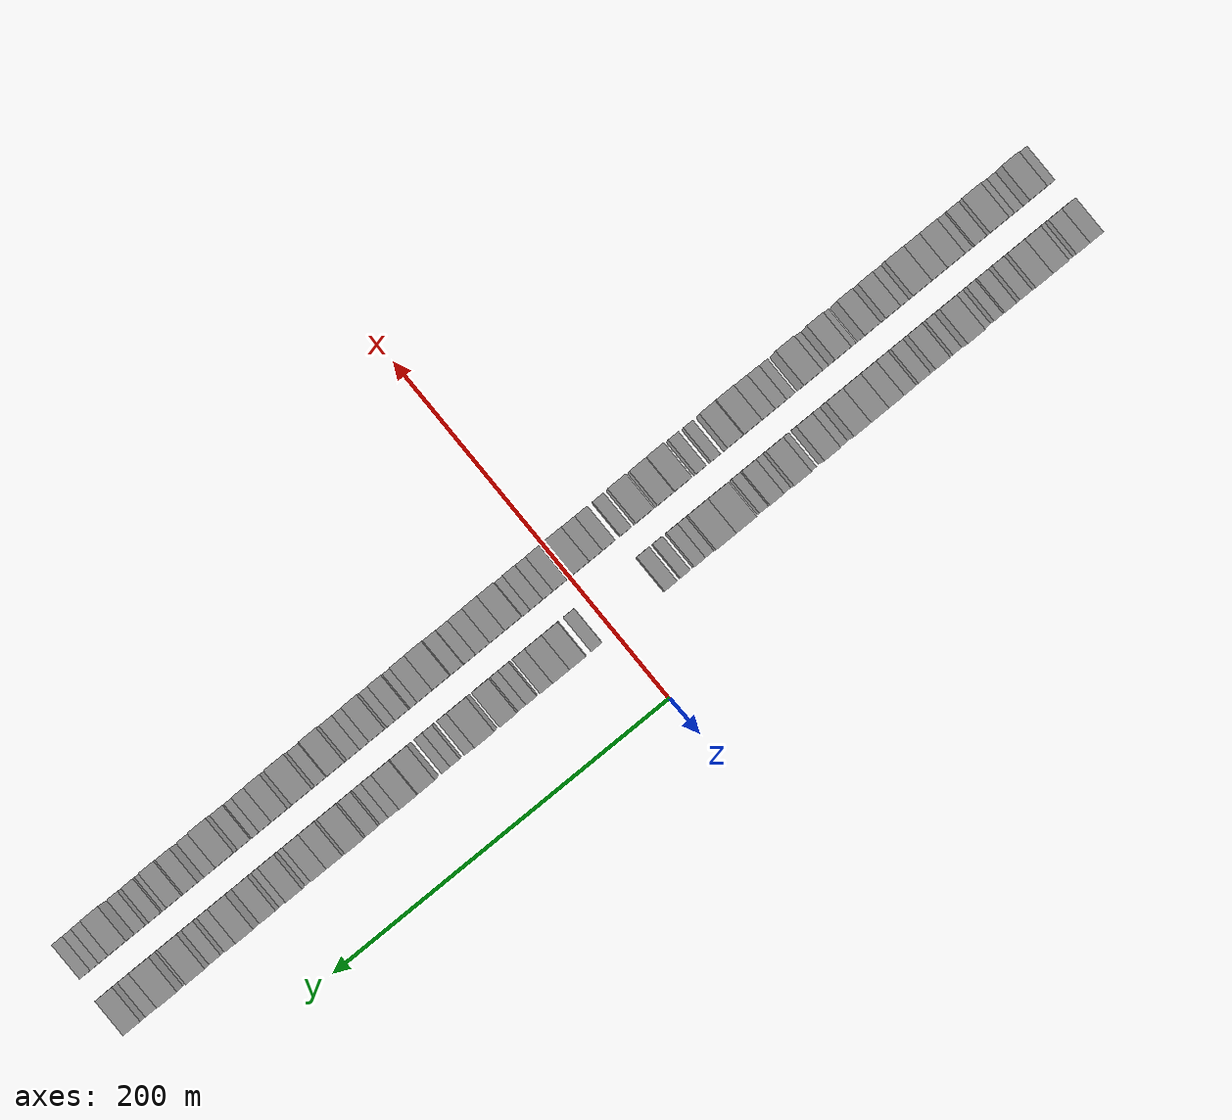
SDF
<sdf version="1.6">
 <world name="default">
  <scene>
   <sky><clouds><speed>12</speed></clouds></sky>
   <ambient>0.4 0.4 0.4 1</ambient>
   <background>0.7 0.7 0.7 1</background>
   <shadows>1</shadows>
  </scene>
  <gravity>0 0 -9.8066</gravity>
  <magnetic_field>6e-06 2.3e-05 -4.2e-05</magnetic_field>
  <physics default="0" name="default_physics" type="ode">
   <ode>
    <solver>
     <type>quick</type>
     <iters>10</iters>
     <sor>1.0</sor>
     <use_dynamic_moi_rescaling>0</use_dynamic_moi_rescaling>
    </solver>
    <constraints>
     <cfm>0</cfm>
     <erp>0.2</erp>
     <contact_max_correcting_vel>100</contact_max_correcting_vel>
     <contact_surface_layer>0.001</contact_surface_layer>
    </constraints>
   </ode>
   <max_step_size>0.004</max_step_size>
   <real_time_factor>1</real_time_factor>
   <real_time_update_rate>250</real_time_update_rate>
  </physics>
  <light name="sun" type="directional">
   <pose>0 0 10 0 0 0</pose>
   <diffuse>0.8 0.8 0.8 1</diffuse>
   <specular>0.2 0.2 0.2 1</specular>
   <attenuation>
    <range>1000</range>
    <constant>0.9</constant>
    <linear>0.01</linear>
    <quadratic>0.001</quadratic>
   </attenuation>
   <direction>-0.5 0.1 -0.9</direction>
  </light>
  <model name="building_1">
   <static>1</static>
   <pose>50.0000 -280.0418 0 0.000000 0.000000 0.000000</pose>
   <link name="link">
    <pose>0 0 9.00 0 0 0</pose>
    <collision name="collision"><geometry><box><size>20.0000 7.9164 18.0000</size></box></geometry></collision>
    <visual name="visual">
     <cast_shadows>0</cast_shadows>
     <geometry><box><size>20.0000 7.9164 18.0000</size></box></geometry>
     <material>
      <script>
       <uri>model://grey_wall/materials/scripts</uri>
       <uri>model://grey_wall/materials/textures</uri>
       <name>vrc/grey_wall</name>
      </script>
     </material>
    </visual>
   </link>
  </model>
  <model name="building_2">
   <static>1</static>
   <pose>50.0000 -272.1381 0 0.000000 0.000000 0.000000</pose>
   <link name="link">
    <pose>0 0 9.00 0 0 0</pose>
    <collision name="collision"><geometry><box><size>20.0000 7.8909 18.0000</size></box></geometry></collision>
    <visual name="visual">
     <cast_shadows>0</cast_shadows>
     <geometry><box><size>20.0000 7.8909 18.0000</size></box></geometry>
     <material>
      <script>
       <uri>model://grey_wall/materials/scripts</uri>
       <uri>model://grey_wall/materials/textures</uri>
       <name>vrc/grey_wall</name>
      </script>
     </material>
    </visual>
   </link>
  </model>
  <model name="building_3">
   <static>1</static>
   <pose>50.0000 -265.5520 0 0.000000 0.000000 0.000000</pose>
   <link name="link">
    <pose>0 0 6.00 0 0 0</pose>
    <collision name="collision"><geometry><box><size>20.0000 5.2812 12.0000</size></box></geometry></collision>
    <visual name="visual">
     <cast_shadows>0</cast_shadows>
     <geometry><box><size>20.0000 5.2812 12.0000</size></box></geometry>
     <material>
      <script>
       <uri>model://grey_wall/materials/scripts</uri>
       <uri>model://grey_wall/materials/textures</uri>
       <name>vrc/grey_wall</name>
      </script>
     </material>
    </visual>
   </link>
  </model>
  <model name="building_4">
   <static>1</static>
   <pose>50.0000 -258.2314 0 0.000000 0.000000 0.000000</pose>
   <link name="link">
    <pose>0 0 10.50 0 0 0</pose>
    <collision name="collision"><geometry><box><size>20.0000 9.3601 21.0000</size></box></geometry></collision>
    <visual name="visual">
     <cast_shadows>0</cast_shadows>
     <geometry><box><size>20.0000 9.3601 21.0000</size></box></geometry>
     <material>
      <script>
       <uri>model://grey_wall/materials/scripts</uri>
       <uri>model://grey_wall/materials/textures</uri>
       <name>vrc/grey_wall</name>
      </script>
     </material>
    </visual>
   </link>
  </model>
  <model name="building_5">
   <static>1</static>
   <pose>50.0000 -248.5249 0 0.000000 0.000000 0.000000</pose>
   <link name="link">
    <pose>0 0 10.50 0 0 0</pose>
    <collision name="collision"><geometry><box><size>20.0000 10.0527 21.0000</size></box></geometry></collision>
    <visual name="visual">
     <cast_shadows>0</cast_shadows>
     <geometry><box><size>20.0000 10.0527 21.0000</size></box></geometry>
     <material>
      <script>
       <uri>model://grey_wall/materials/scripts</uri>
       <uri>model://grey_wall/materials/textures</uri>
       <name>vrc/grey_wall</name>
      </script>
     </material>
    </visual>
   </link>
  </model>
  <model name="building_6">
   <static>1</static>
   <pose>50.0000 -239.9425 0 0.000000 0.000000 0.000000</pose>
   <link name="link">
    <pose>0 0 7.50 0 0 0</pose>
    <collision name="collision"><geometry><box><size>20.0000 7.1122 15.0000</size></box></geometry></collision>
    <visual name="visual">
     <cast_shadows>0</cast_shadows>
     <geometry><box><size>20.0000 7.1122 15.0000</size></box></geometry>
     <material>
      <script>
       <uri>model://grey_wall/materials/scripts</uri>
       <uri>model://grey_wall/materials/textures</uri>
       <name>vrc/grey_wall</name>
      </script>
     </material>
    </visual>
   </link>
  </model>
  <model name="building_7">
   <static>1</static>
   <pose>50.0000 -230.9137 0 0.000000 0.000000 0.000000</pose>
   <link name="link">
    <pose>0 0 7.50 0 0 0</pose>
    <collision name="collision"><geometry><box><size>20.0000 6.9454 15.0000</size></box></geometry></collision>
    <visual name="visual">
     <cast_shadows>0</cast_shadows>
     <geometry><box><size>20.0000 6.9454 15.0000</size></box></geometry>
     <material>
      <script>
       <uri>model://grey_wall/materials/scripts</uri>
       <uri>model://grey_wall/materials/textures</uri>
       <name>vrc/grey_wall</name>
      </script>
     </material>
    </visual>
   </link>
  </model>
  <model name="building_8">
   <static>1</static>
   <pose>50.0000 -224.8101 0 0.000000 0.000000 0.000000</pose>
   <link name="link">
    <pose>0 0 6.00 0 0 0</pose>
    <collision name="collision"><geometry><box><size>20.0000 5.2617 12.0000</size></box></geometry></collision>
    <visual name="visual">
     <cast_shadows>0</cast_shadows>
     <geometry><box><size>20.0000 5.2617 12.0000</size></box></geometry>
     <material>
      <script>
       <uri>model://grey_wall/materials/scripts</uri>
       <uri>model://grey_wall/materials/textures</uri>
       <name>vrc/grey_wall</name>
      </script>
     </material>
    </visual>
   </link>
  </model>
  <model name="building_9">
   <static>1</static>
   <pose>50.0000 -217.7683 0 0.000000 0.000000 0.000000</pose>
   <link name="link">
    <pose>0 0 6.00 0 0 0</pose>
    <collision name="collision"><geometry><box><size>20.0000 4.8219 12.0000</size></box></geometry></collision>
    <visual name="visual">
     <cast_shadows>0</cast_shadows>
     <geometry><box><size>20.0000 4.8219 12.0000</size></box></geometry>
     <material>
      <script>
       <uri>model://grey_wall/materials/scripts</uri>
       <uri>model://grey_wall/materials/textures</uri>
       <name>vrc/grey_wall</name>
      </script>
     </material>
    </visual>
   </link>
  </model>
  <model name="building_10">
   <static>1</static>
   <pose>50.0000 -208.3083 0 0.000000 0.000000 0.000000</pose>
   <link name="link">
    <pose>0 0 12.00 0 0 0</pose>
    <collision name="collision"><geometry><box><size>20.0000 10.0980 24.0000</size></box></geometry></collision>
    <visual name="visual">
     <cast_shadows>0</cast_shadows>
     <geometry><box><size>20.0000 10.0980 24.0000</size></box></geometry>
     <material>
      <script>
       <uri>model://grey_wall/materials/scripts</uri>
       <uri>model://grey_wall/materials/textures</uri>
       <name>vrc/grey_wall</name>
      </script>
     </material>
    </visual>
   </link>
  </model>
  <model name="building_11">
   <static>1</static>
   <pose>50.0000 -200.6108 0 0.000000 0.000000 0.000000</pose>
   <link name="link">
    <pose>0 0 6.00 0 0 0</pose>
    <collision name="collision"><geometry><box><size>20.0000 5.2971 12.0000</size></box></geometry></collision>
    <visual name="visual">
     <cast_shadows>0</cast_shadows>
     <geometry><box><size>20.0000 5.2971 12.0000</size></box></geometry>
     <material>
      <script>
       <uri>model://grey_wall/materials/scripts</uri>
       <uri>model://grey_wall/materials/textures</uri>
       <name>vrc/grey_wall</name>
      </script>
     </material>
    </visual>
   </link>
  </model>
  <model name="building_12">
   <static>1</static>
   <pose>50.0000 -190.6578 0 0.000000 0.000000 0.000000</pose>
   <link name="link">
    <pose>0 0 9.00 0 0 0</pose>
    <collision name="collision"><geometry><box><size>20.0000 8.6088 18.0000</size></box></geometry></collision>
    <visual name="visual">
     <cast_shadows>0</cast_shadows>
     <geometry><box><size>20.0000 8.6088 18.0000</size></box></geometry>
     <material>
      <script>
       <uri>model://grey_wall/materials/scripts</uri>
       <uri>model://grey_wall/materials/textures</uri>
       <name>vrc/grey_wall</name>
      </script>
     </material>
    </visual>
   </link>
  </model>
  <model name="building_13">
   <static>1</static>
   <pose>50.0000 -180.7270 0 0.000000 0.000000 0.000000</pose>
   <link name="link">
    <pose>0 0 7.50 0 0 0</pose>
    <collision name="collision"><geometry><box><size>20.0000 7.2529 15.0000</size></box></geometry></collision>
    <visual name="visual">
     <cast_shadows>0</cast_shadows>
     <geometry><box><size>20.0000 7.2529 15.0000</size></box></geometry>
     <material>
      <script>
       <uri>model://grey_wall/materials/scripts</uri>
       <uri>model://grey_wall/materials/textures</uri>
       <name>vrc/grey_wall</name>
      </script>
     </material>
    </visual>
   </link>
  </model>
  <model name="building_14">
   <static>1</static>
   <pose>50.0000 -171.2590 0 0.000000 0.000000 0.000000</pose>
   <link name="link">
    <pose>0 0 9.00 0 0 0</pose>
    <collision name="collision"><geometry><box><size>20.0000 7.6830 18.0000</size></box></geometry></collision>
    <visual name="visual">
     <cast_shadows>0</cast_shadows>
     <geometry><box><size>20.0000 7.6830 18.0000</size></box></geometry>
     <material>
      <script>
       <uri>model://grey_wall/materials/scripts</uri>
       <uri>model://grey_wall/materials/textures</uri>
       <name>vrc/grey_wall</name>
      </script>
     </material>
    </visual>
   </link>
  </model>
  <model name="building_15">
   <static>1</static>
   <pose>50.0000 -162.9689 0 0.000000 0.000000 0.000000</pose>
   <link name="link">
    <pose>0 0 10.50 0 0 0</pose>
    <collision name="collision"><geometry><box><size>20.0000 8.8972 21.0000</size></box></geometry></collision>
    <visual name="visual">
     <cast_shadows>0</cast_shadows>
     <geometry><box><size>20.0000 8.8972 21.0000</size></box></geometry>
     <material>
      <script>
       <uri>model://grey_wall/materials/scripts</uri>
       <uri>model://grey_wall/materials/textures</uri>
       <name>vrc/grey_wall</name>
      </script>
     </material>
    </visual>
   </link>
  </model>
  <model name="building_16">
   <static>1</static>
   <pose>50.0000 -153.3643 0 0.000000 0.000000 0.000000</pose>
   <link name="link">
    <pose>0 0 10.50 0 0 0</pose>
    <collision name="collision"><geometry><box><size>20.0000 10.3121 21.0000</size></box></geometry></collision>
    <visual name="visual">
     <cast_shadows>0</cast_shadows>
     <geometry><box><size>20.0000 10.3121 21.0000</size></box></geometry>
     <material>
      <script>
       <uri>model://grey_wall/materials/scripts</uri>
       <uri>model://grey_wall/materials/textures</uri>
       <name>vrc/grey_wall</name>
      </script>
     </material>
    </visual>
   </link>
  </model>
  <model name="building_17">
   <static>1</static>
   <pose>50.0000 -143.2969 0 0.000000 0.000000 0.000000</pose>
   <link name="link">
    <pose>0 0 10.50 0 0 0</pose>
    <collision name="collision"><geometry><box><size>20.0000 9.8226 21.0000</size></box></geometry></collision>
    <visual name="visual">
     <cast_shadows>0</cast_shadows>
     <geometry><box><size>20.0000 9.8226 21.0000</size></box></geometry>
     <material>
      <script>
       <uri>model://grey_wall/materials/scripts</uri>
       <uri>model://grey_wall/materials/textures</uri>
       <name>vrc/grey_wall</name>
      </script>
     </material>
    </visual>
   </link>
  </model>
  <model name="building_18">
   <static>1</static>
   <pose>50.0000 -133.5060 0 0.000000 0.000000 0.000000</pose>
   <link name="link">
    <pose>0 0 6.00 0 0 0</pose>
    <collision name="collision"><geometry><box><size>20.0000 5.7592 12.0000</size></box></geometry></collision>
    <visual name="visual">
     <cast_shadows>0</cast_shadows>
     <geometry><box><size>20.0000 5.7592 12.0000</size></box></geometry>
     <material>
      <script>
       <uri>model://grey_wall/materials/scripts</uri>
       <uri>model://grey_wall/materials/textures</uri>
       <name>vrc/grey_wall</name>
      </script>
     </material>
    </visual>
   </link>
  </model>
  <model name="building_19">
   <static>1</static>
   <pose>50.0000 -125.8927 0 0.000000 0.000000 0.000000</pose>
   <link name="link">
    <pose>0 0 10.50 0 0 0</pose>
    <collision name="collision"><geometry><box><size>20.0000 9.4675 21.0000</size></box></geometry></collision>
    <visual name="visual">
     <cast_shadows>0</cast_shadows>
     <geometry><box><size>20.0000 9.4675 21.0000</size></box></geometry>
     <material>
      <script>
       <uri>model://grey_wall/materials/scripts</uri>
       <uri>model://grey_wall/materials/textures</uri>
       <name>vrc/grey_wall</name>
      </script>
     </material>
    </visual>
   </link>
  </model>
  <model name="building_20">
   <static>1</static>
   <pose>50.0000 -115.6931 0 0.000000 0.000000 0.000000</pose>
   <link name="link">
    <pose>0 0 6.00 0 0 0</pose>
    <collision name="collision"><geometry><box><size>20.0000 4.9316 12.0000</size></box></geometry></collision>
    <visual name="visual">
     <cast_shadows>0</cast_shadows>
     <geometry><box><size>20.0000 4.9316 12.0000</size></box></geometry>
     <material>
      <script>
       <uri>model://grey_wall/materials/scripts</uri>
       <uri>model://grey_wall/materials/textures</uri>
       <name>vrc/grey_wall</name>
      </script>
     </material>
    </visual>
   </link>
  </model>
  <model name="building_21">
   <static>1</static>
   <pose>50.0000 -108.1800 0 0.000000 0.000000 0.000000</pose>
   <link name="link">
    <pose>0 0 12.00 0 0 0</pose>
    <collision name="collision"><geometry><box><size>20.0000 10.0948 24.0000</size></box></geometry></collision>
    <visual name="visual">
     <cast_shadows>0</cast_shadows>
     <geometry><box><size>20.0000 10.0948 24.0000</size></box></geometry>
     <material>
      <script>
       <uri>model://grey_wall/materials/scripts</uri>
       <uri>model://grey_wall/materials/textures</uri>
       <name>vrc/grey_wall</name>
      </script>
     </material>
    </visual>
   </link>
  </model>
  <model name="building_22">
   <static>1</static>
   <pose>50.0000 -100.7014 0 0.000000 0.000000 0.000000</pose>
   <link name="link">
    <pose>0 0 6.00 0 0 0</pose>
    <collision name="collision"><geometry><box><size>20.0000 4.8624 12.0000</size></box></geometry></collision>
    <visual name="visual">
     <cast_shadows>0</cast_shadows>
     <geometry><box><size>20.0000 4.8624 12.0000</size></box></geometry>
     <material>
      <script>
       <uri>model://grey_wall/materials/scripts</uri>
       <uri>model://grey_wall/materials/textures</uri>
       <name>vrc/grey_wall</name>
      </script>
     </material>
    </visual>
   </link>
  </model>
  <model name="building_23">
   <static>1</static>
   <pose>50.0000 -94.0933 0 0.000000 0.000000 0.000000</pose>
   <link name="link">
    <pose>0 0 9.00 0 0 0</pose>
    <collision name="collision"><geometry><box><size>20.0000 8.3538 18.0000</size></box></geometry></collision>
    <visual name="visual">
     <cast_shadows>0</cast_shadows>
     <geometry><box><size>20.0000 8.3538 18.0000</size></box></geometry>
     <material>
      <script>
       <uri>model://grey_wall/materials/scripts</uri>
       <uri>model://grey_wall/materials/textures</uri>
       <name>vrc/grey_wall</name>
      </script>
     </material>
    </visual>
   </link>
  </model>
  <model name="building_24">
   <static>1</static>
   <pose>50.0000 -87.2946 0 0.000000 0.000000 0.000000</pose>
   <link name="link">
    <pose>0 0 6.00 0 0 0</pose>
    <collision name="collision"><geometry><box><size>20.0000 5.2435 12.0000</size></box></geometry></collision>
    <visual name="visual">
     <cast_shadows>0</cast_shadows>
     <geometry><box><size>20.0000 5.2435 12.0000</size></box></geometry>
     <material>
      <script>
       <uri>model://grey_wall/materials/scripts</uri>
       <uri>model://grey_wall/materials/textures</uri>
       <name>vrc/grey_wall</name>
      </script>
     </material>
    </visual>
   </link>
  </model>
  <model name="building_25">
   <static>1</static>
   <pose>50.0000 -75.7288 0 0.000000 0.000000 0.000000</pose>
   <link name="link">
    <pose>0 0 12.00 0 0 0</pose>
    <collision name="collision"><geometry><box><size>20.0000 11.8882 24.0000</size></box></geometry></collision>
    <visual name="visual">
     <cast_shadows>0</cast_shadows>
     <geometry><box><size>20.0000 11.8882 24.0000</size></box></geometry>
     <material>
      <script>
       <uri>model://grey_wall/materials/scripts</uri>
       <uri>model://grey_wall/materials/textures</uri>
       <name>vrc/grey_wall</name>
      </script>
     </material>
    </visual>
   </link>
  </model>
  <model name="building_26">
   <static>1</static>
   <pose>50.0000 -63.8923 0 0.000000 0.000000 0.000000</pose>
   <link name="link">
    <pose>0 0 12.00 0 0 0</pose>
    <collision name="collision"><geometry><box><size>20.0000 11.7849 24.0000</size></box></geometry></collision>
    <visual name="visual">
     <cast_shadows>0</cast_shadows>
     <geometry><box><size>20.0000 11.7849 24.0000</size></box></geometry>
     <material>
      <script>
       <uri>model://grey_wall/materials/scripts</uri>
       <uri>model://grey_wall/materials/textures</uri>
       <name>vrc/grey_wall</name>
      </script>
     </material>
    </visual>
   </link>
  </model>
  <model name="building_27">
   <static>1</static>
   <pose>50.0000 -55.4154 0 0.000000 0.000000 0.000000</pose>
   <link name="link">
    <pose>0 0 6.00 0 0 0</pose>
    <collision name="collision"><geometry><box><size>20.0000 5.1688 12.0000</size></box></geometry></collision>
    <visual name="visual">
     <cast_shadows>0</cast_shadows>
     <geometry><box><size>20.0000 5.1688 12.0000</size></box></geometry>
     <material>
      <script>
       <uri>model://grey_wall/materials/scripts</uri>
       <uri>model://grey_wall/materials/textures</uri>
       <name>vrc/grey_wall</name>
      </script>
     </material>
    </visual>
   </link>
  </model>
  <model name="building_28">
   <static>1</static>
   <pose>50.0000 -49.5430 0 0.000000 0.000000 0.000000</pose>
   <link name="link">
    <pose>0 0 7.50 0 0 0</pose>
    <collision name="collision"><geometry><box><size>20.0000 6.5759 15.0000</size></box></geometry></collision>
    <visual name="visual">
     <cast_shadows>0</cast_shadows>
     <geometry><box><size>20.0000 6.5759 15.0000</size></box></geometry>
     <material>
      <script>
       <uri>model://grey_wall/materials/scripts</uri>
       <uri>model://grey_wall/materials/textures</uri>
       <name>vrc/grey_wall</name>
      </script>
     </material>
    </visual>
   </link>
  </model>
  <model name="building_29">
   <static>1</static>
   <pose>50.0000 -41.3061 0 0.000000 0.000000 0.000000</pose>
   <link name="link">
    <pose>0 0 6.00 0 0 0</pose>
    <collision name="collision"><geometry><box><size>20.0000 5.8980 12.0000</size></box></geometry></collision>
    <visual name="visual">
     <cast_shadows>0</cast_shadows>
     <geometry><box><size>20.0000 5.8980 12.0000</size></box></geometry>
     <material>
      <script>
       <uri>model://grey_wall/materials/scripts</uri>
       <uri>model://grey_wall/materials/textures</uri>
       <name>vrc/grey_wall</name>
      </script>
     </material>
    </visual>
   </link>
  </model>
  <model name="building_30">
   <static>1</static>
   <pose>50.0000 -32.6399 0 0.000000 0.000000 0.000000</pose>
   <link name="link">
    <pose>0 0 7.50 0 0 0</pose>
    <collision name="collision"><geometry><box><size>20.0000 7.4343 15.0000</size></box></geometry></collision>
    <visual name="visual">
     <cast_shadows>0</cast_shadows>
     <geometry><box><size>20.0000 7.4343 15.0000</size></box></geometry>
     <material>
      <script>
       <uri>model://grey_wall/materials/scripts</uri>
       <uri>model://grey_wall/materials/textures</uri>
       <name>vrc/grey_wall</name>
      </script>
     </material>
    </visual>
   </link>
  </model>
  <model name="building_31">
   <static>1</static>
   <pose>50.0000 10.7931 0 0.000000 0.000000 0.000000</pose>
   <link name="link">
    <pose>0 0 7.50 0 0 0</pose>
    <collision name="collision"><geometry><box><size>20.0000 6.4772 15.0000</size></box></geometry></collision>
    <visual name="visual">
     <cast_shadows>0</cast_shadows>
     <geometry><box><size>20.0000 6.4772 15.0000</size></box></geometry>
     <material>
      <script>
       <uri>model://grey_wall/materials/scripts</uri>
       <uri>model://grey_wall/materials/textures</uri>
       <name>vrc/grey_wall</name>
      </script>
     </material>
    </visual>
   </link>
  </model>
  <model name="building_32">
   <static>1</static>
   <pose>50.0000 21.7320 0 0.000000 0.000000 0.000000</pose>
   <link name="link">
    <pose>0 0 10.50 0 0 0</pose>
    <collision name="collision"><geometry><box><size>20.0000 9.4007 21.0000</size></box></geometry></collision>
    <visual name="visual">
     <cast_shadows>0</cast_shadows>
     <geometry><box><size>20.0000 9.4007 21.0000</size></box></geometry>
     <material>
      <script>
       <uri>model://grey_wall/materials/scripts</uri>
       <uri>model://grey_wall/materials/textures</uri>
       <name>vrc/grey_wall</name>
      </script>
     </material>
    </visual>
   </link>
  </model>
  <model name="building_33">
   <static>1</static>
   <pose>50.0000 31.3498 0 0.000000 0.000000 0.000000</pose>
   <link name="link">
    <pose>0 0 10.50 0 0 0</pose>
    <collision name="collision"><geometry><box><size>20.0000 9.8350 21.0000</size></box></geometry></collision>
    <visual name="visual">
     <cast_shadows>0</cast_shadows>
     <geometry><box><size>20.0000 9.8350 21.0000</size></box></geometry>
     <material>
      <script>
       <uri>model://grey_wall/materials/scripts</uri>
       <uri>model://grey_wall/materials/textures</uri>
       <name>vrc/grey_wall</name>
      </script>
     </material>
    </visual>
   </link>
  </model>
  <model name="building_34">
   <static>1</static>
   <pose>50.0000 39.9967 0 0.000000 0.000000 0.000000</pose>
   <link name="link">
    <pose>0 0 9.00 0 0 0</pose>
    <collision name="collision"><geometry><box><size>20.0000 7.4589 18.0000</size></box></geometry></collision>
    <visual name="visual">
     <cast_shadows>0</cast_shadows>
     <geometry><box><size>20.0000 7.4589 18.0000</size></box></geometry>
     <material>
      <script>
       <uri>model://grey_wall/materials/scripts</uri>
       <uri>model://grey_wall/materials/textures</uri>
       <name>vrc/grey_wall</name>
      </script>
     </material>
    </visual>
   </link>
  </model>
  <model name="building_35">
   <static>1</static>
   <pose>50.0000 48.8616 0 0.000000 0.000000 0.000000</pose>
   <link name="link">
    <pose>0 0 7.50 0 0 0</pose>
    <collision name="collision"><geometry><box><size>20.0000 6.2709 15.0000</size></box></geometry></collision>
    <visual name="visual">
     <cast_shadows>0</cast_shadows>
     <geometry><box><size>20.0000 6.2709 15.0000</size></box></geometry>
     <material>
      <script>
       <uri>model://grey_wall/materials/scripts</uri>
       <uri>model://grey_wall/materials/textures</uri>
       <name>vrc/grey_wall</name>
      </script>
     </material>
    </visual>
   </link>
  </model>
  <model name="building_36">
   <static>1</static>
   <pose>50.0000 54.4242 0 0.000000 0.000000 0.000000</pose>
   <link name="link">
    <pose>0 0 6.00 0 0 0</pose>
    <collision name="collision"><geometry><box><size>20.0000 4.8543 12.0000</size></box></geometry></collision>
    <visual name="visual">
     <cast_shadows>0</cast_shadows>
     <geometry><box><size>20.0000 4.8543 12.0000</size></box></geometry>
     <material>
      <script>
       <uri>model://grey_wall/materials/scripts</uri>
       <uri>model://grey_wall/materials/textures</uri>
       <name>vrc/grey_wall</name>
      </script>
     </material>
    </visual>
   </link>
  </model>
  <model name="building_37">
   <static>1</static>
   <pose>50.0000 61.8601 0 0.000000 0.000000 0.000000</pose>
   <link name="link">
    <pose>0 0 12.00 0 0 0</pose>
    <collision name="collision"><geometry><box><size>20.0000 10.0174 24.0000</size></box></geometry></collision>
    <visual name="visual">
     <cast_shadows>0</cast_shadows>
     <geometry><box><size>20.0000 10.0174 24.0000</size></box></geometry>
     <material>
      <script>
       <uri>model://grey_wall/materials/scripts</uri>
       <uri>model://grey_wall/materials/textures</uri>
       <name>vrc/grey_wall</name>
      </script>
     </material>
    </visual>
   </link>
  </model>
  <model name="building_38">
   <static>1</static>
   <pose>50.0000 75.5891 0 0.000000 0.000000 0.000000</pose>
   <link name="link">
    <pose>0 0 12.00 0 0 0</pose>
    <collision name="collision"><geometry><box><size>20.0000 11.4407 24.0000</size></box></geometry></collision>
    <visual name="visual">
     <cast_shadows>0</cast_shadows>
     <geometry><box><size>20.0000 11.4407 24.0000</size></box></geometry>
     <material>
      <script>
       <uri>model://grey_wall/materials/scripts</uri>
       <uri>model://grey_wall/materials/textures</uri>
       <name>vrc/grey_wall</name>
      </script>
     </material>
    </visual>
   </link>
  </model>
  <model name="building_39">
   <static>1</static>
   <pose>50.0000 84.5925 0 0.000000 0.000000 0.000000</pose>
   <link name="link">
    <pose>0 0 7.50 0 0 0</pose>
    <collision name="collision"><geometry><box><size>20.0000 6.5662 15.0000</size></box></geometry></collision>
    <visual name="visual">
     <cast_shadows>0</cast_shadows>
     <geometry><box><size>20.0000 6.5662 15.0000</size></box></geometry>
     <material>
      <script>
       <uri>model://grey_wall/materials/scripts</uri>
       <uri>model://grey_wall/materials/textures</uri>
       <name>vrc/grey_wall</name>
      </script>
     </material>
    </visual>
   </link>
  </model>
  <model name="building_40">
   <static>1</static>
   <pose>50.0000 93.7142 0 0.000000 0.000000 0.000000</pose>
   <link name="link">
    <pose>0 0 6.00 0 0 0</pose>
    <collision name="collision"><geometry><box><size>20.0000 5.6771 12.0000</size></box></geometry></collision>
    <visual name="visual">
     <cast_shadows>0</cast_shadows>
     <geometry><box><size>20.0000 5.6771 12.0000</size></box></geometry>
     <material>
      <script>
       <uri>model://grey_wall/materials/scripts</uri>
       <uri>model://grey_wall/materials/textures</uri>
       <name>vrc/grey_wall</name>
      </script>
     </material>
    </visual>
   </link>
  </model>
  <model name="building_41">
   <static>1</static>
   <pose>50.0000 99.0302 0 0.000000 0.000000 0.000000</pose>
   <link name="link">
    <pose>0 0 6.00 0 0 0</pose>
    <collision name="collision"><geometry><box><size>20.0000 4.9550 12.0000</size></box></geometry></collision>
    <visual name="visual">
     <cast_shadows>0</cast_shadows>
     <geometry><box><size>20.0000 4.9550 12.0000</size></box></geometry>
     <material>
      <script>
       <uri>model://grey_wall/materials/scripts</uri>
       <uri>model://grey_wall/materials/textures</uri>
       <name>vrc/grey_wall</name>
      </script>
     </material>
    </visual>
   </link>
  </model>
  <model name="building_42">
   <static>1</static>
   <pose>50.0000 109.4986 0 0.000000 0.000000 0.000000</pose>
   <link name="link">
    <pose>0 0 10.50 0 0 0</pose>
    <collision name="collision"><geometry><box><size>20.0000 9.9817 21.0000</size></box></geometry></collision>
    <visual name="visual">
     <cast_shadows>0</cast_shadows>
     <geometry><box><size>20.0000 9.9817 21.0000</size></box></geometry>
     <material>
      <script>
       <uri>model://grey_wall/materials/scripts</uri>
       <uri>model://grey_wall/materials/textures</uri>
       <name>vrc/grey_wall</name>
      </script>
     </material>
    </visual>
   </link>
  </model>
  <model name="building_43">
   <static>1</static>
   <pose>50.0000 119.6205 0 0.000000 0.000000 0.000000</pose>
   <link name="link">
    <pose>0 0 12.00 0 0 0</pose>
    <collision name="collision"><geometry><box><size>20.0000 10.2622 24.0000</size></box></geometry></collision>
    <visual name="visual">
     <cast_shadows>0</cast_shadows>
     <geometry><box><size>20.0000 10.2622 24.0000</size></box></geometry>
     <material>
      <script>
       <uri>model://grey_wall/materials/scripts</uri>
       <uri>model://grey_wall/materials/textures</uri>
       <name>vrc/grey_wall</name>
      </script>
     </material>
    </visual>
   </link>
  </model>
  <model name="building_44">
   <static>1</static>
   <pose>50.0000 128.4850 0 0.000000 0.000000 0.000000</pose>
   <link name="link">
    <pose>0 0 7.50 0 0 0</pose>
    <collision name="collision"><geometry><box><size>20.0000 7.4667 15.0000</size></box></geometry></collision>
    <visual name="visual">
     <cast_shadows>0</cast_shadows>
     <geometry><box><size>20.0000 7.4667 15.0000</size></box></geometry>
     <material>
      <script>
       <uri>model://grey_wall/materials/scripts</uri>
       <uri>model://grey_wall/materials/textures</uri>
       <name>vrc/grey_wall</name>
      </script>
     </material>
    </visual>
   </link>
  </model>
  <model name="building_45">
   <static>1</static>
   <pose>50.0000 134.9356 0 0.000000 0.000000 0.000000</pose>
   <link name="link">
    <pose>0 0 6.00 0 0 0</pose>
    <collision name="collision"><geometry><box><size>20.0000 5.4345 12.0000</size></box></geometry></collision>
    <visual name="visual">
     <cast_shadows>0</cast_shadows>
     <geometry><box><size>20.0000 5.4345 12.0000</size></box></geometry>
     <material>
      <script>
       <uri>model://grey_wall/materials/scripts</uri>
       <uri>model://grey_wall/materials/textures</uri>
       <name>vrc/grey_wall</name>
      </script>
     </material>
    </visual>
   </link>
  </model>
  <model name="building_46">
   <static>1</static>
   <pose>50.0000 141.3621 0 0.000000 0.000000 0.000000</pose>
   <link name="link">
    <pose>0 0 9.00 0 0 0</pose>
    <collision name="collision"><geometry><box><size>20.0000 7.4186 18.0000</size></box></geometry></collision>
    <visual name="visual">
     <cast_shadows>0</cast_shadows>
     <geometry><box><size>20.0000 7.4186 18.0000</size></box></geometry>
     <material>
      <script>
       <uri>model://grey_wall/materials/scripts</uri>
       <uri>model://grey_wall/materials/textures</uri>
       <name>vrc/grey_wall</name>
      </script>
     </material>
    </visual>
   </link>
  </model>
  <model name="building_47">
   <static>1</static>
   <pose>50.0000 150.5891 0 0.000000 0.000000 0.000000</pose>
   <link name="link">
    <pose>0 0 12.00 0 0 0</pose>
    <collision name="collision"><geometry><box><size>20.0000 11.0352 24.0000</size></box></geometry></collision>
    <visual name="visual">
     <cast_shadows>0</cast_shadows>
     <geometry><box><size>20.0000 11.0352 24.0000</size></box></geometry>
     <material>
      <script>
       <uri>model://grey_wall/materials/scripts</uri>
       <uri>model://grey_wall/materials/textures</uri>
       <name>vrc/grey_wall</name>
      </script>
     </material>
    </visual>
   </link>
  </model>
  <model name="building_48">
   <static>1</static>
   <pose>50.0000 162.7704 0 0.000000 0.000000 0.000000</pose>
   <link name="link">
    <pose>0 0 10.50 0 0 0</pose>
    <collision name="collision"><geometry><box><size>20.0000 9.3275 21.0000</size></box></geometry></collision>
    <visual name="visual">
     <cast_shadows>0</cast_shadows>
     <geometry><box><size>20.0000 9.3275 21.0000</size></box></geometry>
     <material>
      <script>
       <uri>model://grey_wall/materials/scripts</uri>
       <uri>model://grey_wall/materials/textures</uri>
       <name>vrc/grey_wall</name>
      </script>
     </material>
    </visual>
   </link>
  </model>
  <model name="building_49">
   <static>1</static>
   <pose>50.0000 171.9692 0 0.000000 0.000000 0.000000</pose>
   <link name="link">
    <pose>0 0 10.50 0 0 0</pose>
    <collision name="collision"><geometry><box><size>20.0000 9.0700 21.0000</size></box></geometry></collision>
    <visual name="visual">
     <cast_shadows>0</cast_shadows>
     <geometry><box><size>20.0000 9.0700 21.0000</size></box></geometry>
     <material>
      <script>
       <uri>model://grey_wall/materials/scripts</uri>
       <uri>model://grey_wall/materials/textures</uri>
       <name>vrc/grey_wall</name>
      </script>
     </material>
    </visual>
   </link>
  </model>
  <model name="building_50">
   <static>1</static>
   <pose>50.0000 178.9733 0 0.000000 0.000000 0.000000</pose>
   <link name="link">
    <pose>0 0 6.00 0 0 0</pose>
    <collision name="collision"><geometry><box><size>20.0000 4.9381 12.0000</size></box></geometry></collision>
    <visual name="visual">
     <cast_shadows>0</cast_shadows>
     <geometry><box><size>20.0000 4.9381 12.0000</size></box></geometry>
     <material>
      <script>
       <uri>model://grey_wall/materials/scripts</uri>
       <uri>model://grey_wall/materials/textures</uri>
       <name>vrc/grey_wall</name>
      </script>
     </material>
    </visual>
   </link>
  </model>
  <model name="building_51">
   <static>1</static>
   <pose>50.0000 186.2289 0 0.000000 0.000000 0.000000</pose>
   <link name="link">
    <pose>0 0 10.50 0 0 0</pose>
    <collision name="collision"><geometry><box><size>20.0000 9.5733 21.0000</size></box></geometry></collision>
    <visual name="visual">
     <cast_shadows>0</cast_shadows>
     <geometry><box><size>20.0000 9.5733 21.0000</size></box></geometry>
     <material>
      <script>
       <uri>model://grey_wall/materials/scripts</uri>
       <uri>model://grey_wall/materials/textures</uri>
       <name>vrc/grey_wall</name>
      </script>
     </material>
    </visual>
   </link>
  </model>
  <model name="building_52">
   <static>1</static>
   <pose>50.0000 193.9104 0 0.000000 0.000000 0.000000</pose>
   <link name="link">
    <pose>0 0 6.00 0 0 0</pose>
    <collision name="collision"><geometry><box><size>20.0000 5.7896 12.0000</size></box></geometry></collision>
    <visual name="visual">
     <cast_shadows>0</cast_shadows>
     <geometry><box><size>20.0000 5.7896 12.0000</size></box></geometry>
     <material>
      <script>
       <uri>model://grey_wall/materials/scripts</uri>
       <uri>model://grey_wall/materials/textures</uri>
       <name>vrc/grey_wall</name>
      </script>
     </material>
    </visual>
   </link>
  </model>
  <model name="building_53">
   <static>1</static>
   <pose>50.0000 201.4157 0 0.000000 0.000000 0.000000</pose>
   <link name="link">
    <pose>0 0 10.50 0 0 0</pose>
    <collision name="collision"><geometry><box><size>20.0000 9.2210 21.0000</size></box></geometry></collision>
    <visual name="visual">
     <cast_shadows>0</cast_shadows>
     <geometry><box><size>20.0000 9.2210 21.0000</size></box></geometry>
     <material>
      <script>
       <uri>model://grey_wall/materials/scripts</uri>
       <uri>model://grey_wall/materials/textures</uri>
       <name>vrc/grey_wall</name>
      </script>
     </material>
    </visual>
   </link>
  </model>
  <model name="building_54">
   <static>1</static>
   <pose>50.0000 214.1235 0 0.000000 0.000000 0.000000</pose>
   <link name="link">
    <pose>0 0 12.00 0 0 0</pose>
    <collision name="collision"><geometry><box><size>20.0000 10.1945 24.0000</size></box></geometry></collision>
    <visual name="visual">
     <cast_shadows>0</cast_shadows>
     <geometry><box><size>20.0000 10.1945 24.0000</size></box></geometry>
     <material>
      <script>
       <uri>model://grey_wall/materials/scripts</uri>
       <uri>model://grey_wall/materials/textures</uri>
       <name>vrc/grey_wall</name>
      </script>
     </material>
    </visual>
   </link>
  </model>
  <model name="building_55">
   <static>1</static>
   <pose>50.0000 223.1803 0 0.000000 0.000000 0.000000</pose>
   <link name="link">
    <pose>0 0 9.00 0 0 0</pose>
    <collision name="collision"><geometry><box><size>20.0000 7.9191 18.0000</size></box></geometry></collision>
    <visual name="visual">
     <cast_shadows>0</cast_shadows>
     <geometry><box><size>20.0000 7.9191 18.0000</size></box></geometry>
     <material>
      <script>
       <uri>model://grey_wall/materials/scripts</uri>
       <uri>model://grey_wall/materials/textures</uri>
       <name>vrc/grey_wall</name>
      </script>
     </material>
    </visual>
   </link>
  </model>
  <model name="building_56">
   <static>1</static>
   <pose>50.0000 233.5249 0 0.000000 0.000000 0.000000</pose>
   <link name="link">
    <pose>0 0 7.50 0 0 0</pose>
    <collision name="collision"><geometry><box><size>20.0000 6.7701 15.0000</size></box></geometry></collision>
    <visual name="visual">
     <cast_shadows>0</cast_shadows>
     <geometry><box><size>20.0000 6.7701 15.0000</size></box></geometry>
     <material>
      <script>
       <uri>model://grey_wall/materials/scripts</uri>
       <uri>model://grey_wall/materials/textures</uri>
       <name>vrc/grey_wall</name>
      </script>
     </material>
    </visual>
   </link>
  </model>
  <model name="building_57">
   <static>1</static>
   <pose>50.0000 242.4495 0 0.000000 0.000000 0.000000</pose>
   <link name="link">
    <pose>0 0 12.00 0 0 0</pose>
    <collision name="collision"><geometry><box><size>20.0000 11.0789 24.0000</size></box></geometry></collision>
    <visual name="visual">
     <cast_shadows>0</cast_shadows>
     <geometry><box><size>20.0000 11.0789 24.0000</size></box></geometry>
     <material>
      <script>
       <uri>model://grey_wall/materials/scripts</uri>
       <uri>model://grey_wall/materials/textures</uri>
       <name>vrc/grey_wall</name>
      </script>
     </material>
    </visual>
   </link>
  </model>
  <model name="building_58">
   <static>1</static>
   <pose>50.0000 250.5043 0 0.000000 0.000000 0.000000</pose>
   <link name="link">
    <pose>0 0 6.00 0 0 0</pose>
    <collision name="collision"><geometry><box><size>20.0000 5.0308 12.0000</size></box></geometry></collision>
    <visual name="visual">
     <cast_shadows>0</cast_shadows>
     <geometry><box><size>20.0000 5.0308 12.0000</size></box></geometry>
     <material>
      <script>
       <uri>model://grey_wall/materials/scripts</uri>
       <uri>model://grey_wall/materials/textures</uri>
       <name>vrc/grey_wall</name>
      </script>
     </material>
    </visual>
   </link>
  </model>
  <model name="building_59">
   <static>1</static>
   <pose>50.0000 258.8206 0 0.000000 0.000000 0.000000</pose>
   <link name="link">
    <pose>0 0 12.00 0 0 0</pose>
    <collision name="collision"><geometry><box><size>20.0000 11.6018 24.0000</size></box></geometry></collision>
    <visual name="visual">
     <cast_shadows>0</cast_shadows>
     <geometry><box><size>20.0000 11.6018 24.0000</size></box></geometry>
     <material>
      <script>
       <uri>model://grey_wall/materials/scripts</uri>
       <uri>model://grey_wall/materials/textures</uri>
       <name>vrc/grey_wall</name>
      </script>
     </material>
    </visual>
   </link>
  </model>
  <model name="building_60">
   <static>1</static>
   <pose>50.0000 268.8721 0 0.000000 0.000000 0.000000</pose>
   <link name="link">
    <pose>0 0 9.00 0 0 0</pose>
    <collision name="collision"><geometry><box><size>20.0000 8.5012 18.0000</size></box></geometry></collision>
    <visual name="visual">
     <cast_shadows>0</cast_shadows>
     <geometry><box><size>20.0000 8.5012 18.0000</size></box></geometry>
     <material>
      <script>
       <uri>model://grey_wall/materials/scripts</uri>
       <uri>model://grey_wall/materials/textures</uri>
       <name>vrc/grey_wall</name>
      </script>
     </material>
    </visual>
   </link>
  </model>
  <model name="building_61">
   <static>1</static>
   <pose>50.0000 280.1380 0 0.000000 0.000000 0.000000</pose>
   <link name="link">
    <pose>0 0 10.50 0 0 0</pose>
    <collision name="collision"><geometry><box><size>20.0000 10.0306 21.0000</size></box></geometry></collision>
    <visual name="visual">
     <cast_shadows>0</cast_shadows>
     <geometry><box><size>20.0000 10.0306 21.0000</size></box></geometry>
     <material>
      <script>
       <uri>model://grey_wall/materials/scripts</uri>
       <uri>model://grey_wall/materials/textures</uri>
       <name>vrc/grey_wall</name>
      </script>
     </material>
    </visual>
   </link>
  </model>
  <model name="building_62">
   <static>1</static>
   <pose>82.0000 -281.1718 0 0.000000 0.000000 0.000000</pose>
   <link name="link">
    <pose>0 0 6.00 0 0 0</pose>
    <collision name="collision"><geometry><box><size>20.0000 5.6565 12.0000</size></box></geometry></collision>
    <visual name="visual">
     <cast_shadows>0</cast_shadows>
     <geometry><box><size>20.0000 5.6565 12.0000</size></box></geometry>
     <material>
      <script>
       <uri>model://grey_wall/materials/scripts</uri>
       <uri>model://grey_wall/materials/textures</uri>
       <name>vrc/grey_wall</name>
      </script>
     </material>
    </visual>
   </link>
  </model>
  <model name="building_63">
   <static>1</static>
   <pose>82.0000 -270.3287 0 0.000000 0.000000 0.000000</pose>
   <link name="link">
    <pose>0 0 12.00 0 0 0</pose>
    <collision name="collision"><geometry><box><size>20.0000 10.0295 24.0000</size></box></geometry></collision>
    <visual name="visual">
     <cast_shadows>0</cast_shadows>
     <geometry><box><size>20.0000 10.0295 24.0000</size></box></geometry>
     <material>
      <script>
       <uri>model://grey_wall/materials/scripts</uri>
       <uri>model://grey_wall/materials/textures</uri>
       <name>vrc/grey_wall</name>
      </script>
     </material>
    </visual>
   </link>
  </model>
  <model name="building_64">
   <static>1</static>
   <pose>82.0000 -262.3726 0 0.000000 0.000000 0.000000</pose>
   <link name="link">
    <pose>0 0 6.00 0 0 0</pose>
    <collision name="collision"><geometry><box><size>20.0000 5.8828 12.0000</size></box></geometry></collision>
    <visual name="visual">
     <cast_shadows>0</cast_shadows>
     <geometry><box><size>20.0000 5.8828 12.0000</size></box></geometry>
     <material>
      <script>
       <uri>model://grey_wall/materials/scripts</uri>
       <uri>model://grey_wall/materials/textures</uri>
       <name>vrc/grey_wall</name>
      </script>
     </material>
    </visual>
   </link>
  </model>
  <model name="building_65">
   <static>1</static>
   <pose>82.0000 -256.4045 0 0.000000 0.000000 0.000000</pose>
   <link name="link">
    <pose>0 0 7.50 0 0 0</pose>
    <collision name="collision"><geometry><box><size>20.0000 6.0533 15.0000</size></box></geometry></collision>
    <visual name="visual">
     <cast_shadows>0</cast_shadows>
     <geometry><box><size>20.0000 6.0533 15.0000</size></box></geometry>
     <material>
      <script>
       <uri>model://grey_wall/materials/scripts</uri>
       <uri>model://grey_wall/materials/textures</uri>
       <name>vrc/grey_wall</name>
      </script>
     </material>
    </visual>
   </link>
  </model>
  <model name="building_66">
   <static>1</static>
   <pose>82.0000 -247.8282 0 0.000000 0.000000 0.000000</pose>
   <link name="link">
    <pose>0 0 12.00 0 0 0</pose>
    <collision name="collision"><geometry><box><size>20.0000 11.0994 24.0000</size></box></geometry></collision>
    <visual name="visual">
     <cast_shadows>0</cast_shadows>
     <geometry><box><size>20.0000 11.0994 24.0000</size></box></geometry>
     <material>
      <script>
       <uri>model://grey_wall/materials/scripts</uri>
       <uri>model://grey_wall/materials/textures</uri>
       <name>vrc/grey_wall</name>
      </script>
     </material>
    </visual>
   </link>
  </model>
  <model name="building_67">
   <static>1</static>
   <pose>82.0000 -238.6579 0 0.000000 0.000000 0.000000</pose>
   <link name="link">
    <pose>0 0 9.00 0 0 0</pose>
    <collision name="collision"><geometry><box><size>20.0000 7.2413 18.0000</size></box></geometry></collision>
    <visual name="visual">
     <cast_shadows>0</cast_shadows>
     <geometry><box><size>20.0000 7.2413 18.0000</size></box></geometry>
     <material>
      <script>
       <uri>model://grey_wall/materials/scripts</uri>
       <uri>model://grey_wall/materials/textures</uri>
       <name>vrc/grey_wall</name>
      </script>
     </material>
    </visual>
   </link>
  </model>
  <model name="building_68">
   <static>1</static>
   <pose>82.0000 -231.9588 0 0.000000 0.000000 0.000000</pose>
   <link name="link">
    <pose>0 0 7.50 0 0 0</pose>
    <collision name="collision"><geometry><box><size>20.0000 6.1569 15.0000</size></box></geometry></collision>
    <visual name="visual">
     <cast_shadows>0</cast_shadows>
     <geometry><box><size>20.0000 6.1569 15.0000</size></box></geometry>
     <material>
      <script>
       <uri>model://grey_wall/materials/scripts</uri>
       <uri>model://grey_wall/materials/textures</uri>
       <name>vrc/grey_wall</name>
      </script>
     </material>
    </visual>
   </link>
  </model>
  <model name="building_69">
   <static>1</static>
   <pose>82.0000 -223.7689 0 0.000000 0.000000 0.000000</pose>
   <link name="link">
    <pose>0 0 10.50 0 0 0</pose>
    <collision name="collision"><geometry><box><size>20.0000 10.2230 21.0000</size></box></geometry></collision>
    <visual name="visual">
     <cast_shadows>0</cast_shadows>
     <geometry><box><size>20.0000 10.2230 21.0000</size></box></geometry>
     <material>
      <script>
       <uri>model://grey_wall/materials/scripts</uri>
       <uri>model://grey_wall/materials/textures</uri>
       <name>vrc/grey_wall</name>
      </script>
     </material>
    </visual>
   </link>
  </model>
  <model name="building_70">
   <static>1</static>
   <pose>82.0000 -213.7481 0 0.000000 0.000000 0.000000</pose>
   <link name="link">
    <pose>0 0 10.50 0 0 0</pose>
    <collision name="collision"><geometry><box><size>20.0000 9.8186 21.0000</size></box></geometry></collision>
    <visual name="visual">
     <cast_shadows>0</cast_shadows>
     <geometry><box><size>20.0000 9.8186 21.0000</size></box></geometry>
     <material>
      <script>
       <uri>model://grey_wall/materials/scripts</uri>
       <uri>model://grey_wall/materials/textures</uri>
       <name>vrc/grey_wall</name>
      </script>
     </material>
    </visual>
   </link>
  </model>
  <model name="building_71">
   <static>1</static>
   <pose>82.0000 -203.3557 0 0.000000 0.000000 0.000000</pose>
   <link name="link">
    <pose>0 0 12.00 0 0 0</pose>
    <collision name="collision"><geometry><box><size>20.0000 10.9661 24.0000</size></box></geometry></collision>
    <visual name="visual">
     <cast_shadows>0</cast_shadows>
     <geometry><box><size>20.0000 10.9661 24.0000</size></box></geometry>
     <material>
      <script>
       <uri>model://grey_wall/materials/scripts</uri>
       <uri>model://grey_wall/materials/textures</uri>
       <name>vrc/grey_wall</name>
      </script>
     </material>
    </visual>
   </link>
  </model>
  <model name="building_72">
   <static>1</static>
   <pose>82.0000 -194.7106 0 0.000000 0.000000 0.000000</pose>
   <link name="link">
    <pose>0 0 7.50 0 0 0</pose>
    <collision name="collision"><geometry><box><size>20.0000 6.3240 15.0000</size></box></geometry></collision>
    <visual name="visual">
     <cast_shadows>0</cast_shadows>
     <geometry><box><size>20.0000 6.3240 15.0000</size></box></geometry>
     <material>
      <script>
       <uri>model://grey_wall/materials/scripts</uri>
       <uri>model://grey_wall/materials/textures</uri>
       <name>vrc/grey_wall</name>
      </script>
     </material>
    </visual>
   </link>
  </model>
  <model name="building_73">
   <static>1</static>
   <pose>82.0000 -187.2484 0 0.000000 0.000000 0.000000</pose>
   <link name="link">
    <pose>0 0 10.50 0 0 0</pose>
    <collision name="collision"><geometry><box><size>20.0000 8.6004 21.0000</size></box></geometry></collision>
    <visual name="visual">
     <cast_shadows>0</cast_shadows>
     <geometry><box><size>20.0000 8.6004 21.0000</size></box></geometry>
     <material>
      <script>
       <uri>model://grey_wall/materials/scripts</uri>
       <uri>model://grey_wall/materials/textures</uri>
       <name>vrc/grey_wall</name>
      </script>
     </material>
    </visual>
   </link>
  </model>
  <model name="building_74">
   <static>1</static>
   <pose>82.0000 -175.3367 0 0.000000 0.000000 0.000000</pose>
   <link name="link">
    <pose>0 0 10.50 0 0 0</pose>
    <collision name="collision"><geometry><box><size>20.0000 9.2229 21.0000</size></box></geometry></collision>
    <visual name="visual">
     <cast_shadows>0</cast_shadows>
     <geometry><box><size>20.0000 9.2229 21.0000</size></box></geometry>
     <material>
      <script>
       <uri>model://grey_wall/materials/scripts</uri>
       <uri>model://grey_wall/materials/textures</uri>
       <name>vrc/grey_wall</name>
      </script>
     </material>
    </visual>
   </link>
  </model>
  <model name="building_75">
   <static>1</static>
   <pose>82.0000 -165.3211 0 0.000000 0.000000 0.000000</pose>
   <link name="link">
    <pose>0 0 6.00 0 0 0</pose>
    <collision name="collision"><geometry><box><size>20.0000 4.8083 12.0000</size></box></geometry></collision>
    <visual name="visual">
     <cast_shadows>0</cast_shadows>
     <geometry><box><size>20.0000 4.8083 12.0000</size></box></geometry>
     <material>
      <script>
       <uri>model://grey_wall/materials/scripts</uri>
       <uri>model://grey_wall/materials/textures</uri>
       <name>vrc/grey_wall</name>
      </script>
     </material>
    </visual>
   </link>
  </model>
  <model name="building_76">
   <static>1</static>
   <pose>82.0000 -158.1637 0 0.000000 0.000000 0.000000</pose>
   <link name="link">
    <pose>0 0 10.50 0 0 0</pose>
    <collision name="collision"><geometry><box><size>20.0000 9.5065 21.0000</size></box></geometry></collision>
    <visual name="visual">
     <cast_shadows>0</cast_shadows>
     <geometry><box><size>20.0000 9.5065 21.0000</size></box></geometry>
     <material>
      <script>
       <uri>model://grey_wall/materials/scripts</uri>
       <uri>model://grey_wall/materials/textures</uri>
       <name>vrc/grey_wall</name>
      </script>
     </material>
    </visual>
   </link>
  </model>
  <model name="building_77">
   <static>1</static>
   <pose>82.0000 -148.5441 0 0.000000 0.000000 0.000000</pose>
   <link name="link">
    <pose>0 0 6.00 0 0 0</pose>
    <collision name="collision"><geometry><box><size>20.0000 5.7327 12.0000</size></box></geometry></collision>
    <visual name="visual">
     <cast_shadows>0</cast_shadows>
     <geometry><box><size>20.0000 5.7327 12.0000</size></box></geometry>
     <material>
      <script>
       <uri>model://grey_wall/materials/scripts</uri>
       <uri>model://grey_wall/materials/textures</uri>
       <name>vrc/grey_wall</name>
      </script>
     </material>
    </visual>
   </link>
  </model>
  <model name="building_78">
   <static>1</static>
   <pose>82.0000 -140.3143 0 0.000000 0.000000 0.000000</pose>
   <link name="link">
    <pose>0 0 12.00 0 0 0</pose>
    <collision name="collision"><geometry><box><size>20.0000 10.7269 24.0000</size></box></geometry></collision>
    <visual name="visual">
     <cast_shadows>0</cast_shadows>
     <geometry><box><size>20.0000 10.7269 24.0000</size></box></geometry>
     <material>
      <script>
       <uri>model://grey_wall/materials/scripts</uri>
       <uri>model://grey_wall/materials/textures</uri>
       <name>vrc/grey_wall</name>
      </script>
     </material>
    </visual>
   </link>
  </model>
  <model name="building_79">
   <static>1</static>
   <pose>82.0000 -129.2408 0 0.000000 0.000000 0.000000</pose>
   <link name="link">
    <pose>0 0 6.00 0 0 0</pose>
    <collision name="collision"><geometry><box><size>20.0000 5.4200 12.0000</size></box></geometry></collision>
    <visual name="visual">
     <cast_shadows>0</cast_shadows>
     <geometry><box><size>20.0000 5.4200 12.0000</size></box></geometry>
     <material>
      <script>
       <uri>model://grey_wall/materials/scripts</uri>
       <uri>model://grey_wall/materials/textures</uri>
       <name>vrc/grey_wall</name>
      </script>
     </material>
    </visual>
   </link>
  </model>
  <model name="building_80">
   <static>1</static>
   <pose>82.0000 -122.9179 0 0.000000 0.000000 0.000000</pose>
   <link name="link">
    <pose>0 0 7.50 0 0 0</pose>
    <collision name="collision"><geometry><box><size>20.0000 7.2259 15.0000</size></box></geometry></collision>
    <visual name="visual">
     <cast_shadows>0</cast_shadows>
     <geometry><box><size>20.0000 7.2259 15.0000</size></box></geometry>
     <material>
      <script>
       <uri>model://grey_wall/materials/scripts</uri>
       <uri>model://grey_wall/materials/textures</uri>
       <name>vrc/grey_wall</name>
      </script>
     </material>
    </visual>
   </link>
  </model>
  <model name="building_81">
   <static>1</static>
   <pose>82.0000 -115.0719 0 0.000000 0.000000 0.000000</pose>
   <link name="link">
    <pose>0 0 9.00 0 0 0</pose>
    <collision name="collision"><geometry><box><size>20.0000 8.4660 18.0000</size></box></geometry></collision>
    <visual name="visual">
     <cast_shadows>0</cast_shadows>
     <geometry><box><size>20.0000 8.4660 18.0000</size></box></geometry>
     <material>
      <script>
       <uri>model://grey_wall/materials/scripts</uri>
       <uri>model://grey_wall/materials/textures</uri>
       <name>vrc/grey_wall</name>
      </script>
     </material>
    </visual>
   </link>
  </model>
  <model name="building_82">
   <static>1</static>
   <pose>82.0000 -105.6387 0 0.000000 0.000000 0.000000</pose>
   <link name="link">
    <pose>0 0 12.00 0 0 0</pose>
    <collision name="collision"><geometry><box><size>20.0000 10.4004 24.0000</size></box></geometry></collision>
    <visual name="visual">
     <cast_shadows>0</cast_shadows>
     <geometry><box><size>20.0000 10.4004 24.0000</size></box></geometry>
     <material>
      <script>
       <uri>model://grey_wall/materials/scripts</uri>
       <uri>model://grey_wall/materials/textures</uri>
       <name>vrc/grey_wall</name>
      </script>
     </material>
    </visual>
   </link>
  </model>
  <model name="building_83">
   <static>1</static>
   <pose>82.0000 -95.8038 0 0.000000 0.000000 0.000000</pose>
   <link name="link">
    <pose>0 0 10.50 0 0 0</pose>
    <collision name="collision"><geometry><box><size>20.0000 9.2695 21.0000</size></box></geometry></collision>
    <visual name="visual">
     <cast_shadows>0</cast_shadows>
     <geometry><box><size>20.0000 9.2695 21.0000</size></box></geometry>
     <material>
      <script>
       <uri>model://grey_wall/materials/scripts</uri>
       <uri>model://grey_wall/materials/textures</uri>
       <name>vrc/grey_wall</name>
      </script>
     </material>
    </visual>
   </link>
  </model>
  <model name="building_84">
   <static>1</static>
   <pose>82.0000 -85.3598 0 0.000000 0.000000 0.000000</pose>
   <link name="link">
    <pose>0 0 6.00 0 0 0</pose>
    <collision name="collision"><geometry><box><size>20.0000 5.6184 12.0000</size></box></geometry></collision>
    <visual name="visual">
     <cast_shadows>0</cast_shadows>
     <geometry><box><size>20.0000 5.6184 12.0000</size></box></geometry>
     <material>
      <script>
       <uri>model://grey_wall/materials/scripts</uri>
       <uri>model://grey_wall/materials/textures</uri>
       <name>vrc/grey_wall</name>
      </script>
     </material>
    </visual>
   </link>
  </model>
  <model name="building_85">
   <static>1</static>
   <pose>82.0000 -76.5153 0 0.000000 0.000000 0.000000</pose>
   <link name="link">
    <pose>0 0 7.50 0 0 0</pose>
    <collision name="collision"><geometry><box><size>20.0000 6.0707 15.0000</size></box></geometry></collision>
    <visual name="visual">
     <cast_shadows>0</cast_shadows>
     <geometry><box><size>20.0000 6.0707 15.0000</size></box></geometry>
     <material>
      <script>
       <uri>model://grey_wall/materials/scripts</uri>
       <uri>model://grey_wall/materials/textures</uri>
       <name>vrc/grey_wall</name>
      </script>
     </material>
    </visual>
   </link>
  </model>
  <model name="building_86">
   <static>1</static>
   <pose>82.0000 -65.4254 0 0.000000 0.000000 0.000000</pose>
   <link name="link">
    <pose>0 0 12.00 0 0 0</pose>
    <collision name="collision"><geometry><box><size>20.0000 10.1092 24.0000</size></box></geometry></collision>
    <visual name="visual">
     <cast_shadows>0</cast_shadows>
     <geometry><box><size>20.0000 10.1092 24.0000</size></box></geometry>
     <material>
      <script>
       <uri>model://grey_wall/materials/scripts</uri>
       <uri>model://grey_wall/materials/textures</uri>
       <name>vrc/grey_wall</name>
      </script>
     </material>
    </visual>
   </link>
  </model>
  <model name="building_87">
   <static>1</static>
   <pose>82.0000 -55.4789 0 0.000000 0.000000 0.000000</pose>
   <link name="link">
    <pose>0 0 10.50 0 0 0</pose>
    <collision name="collision"><geometry><box><size>20.0000 9.7836 21.0000</size></box></geometry></collision>
    <visual name="visual">
     <cast_shadows>0</cast_shadows>
     <geometry><box><size>20.0000 9.7836 21.0000</size></box></geometry>
     <material>
      <script>
       <uri>model://grey_wall/materials/scripts</uri>
       <uri>model://grey_wall/materials/textures</uri>
       <name>vrc/grey_wall</name>
      </script>
     </material>
    </visual>
   </link>
  </model>
  <model name="building_88">
   <static>1</static>
   <pose>82.0000 -43.2314 0 0.000000 0.000000 0.000000</pose>
   <link name="link">
    <pose>0 0 12.00 0 0 0</pose>
    <collision name="collision"><geometry><box><size>20.0000 10.7114 24.0000</size></box></geometry></collision>
    <visual name="visual">
     <cast_shadows>0</cast_shadows>
     <geometry><box><size>20.0000 10.7114 24.0000</size></box></geometry>
     <material>
      <script>
       <uri>model://grey_wall/materials/scripts</uri>
       <uri>model://grey_wall/materials/textures</uri>
       <name>vrc/grey_wall</name>
      </script>
     </material>
    </visual>
   </link>
  </model>
  <model name="building_89">
   <static>1</static>
   <pose>82.0000 -32.5953 0 0.000000 0.000000 0.000000</pose>
   <link name="link">
    <pose>0 0 7.50 0 0 0</pose>
    <collision name="collision"><geometry><box><size>20.0000 6.5607 15.0000</size></box></geometry></collision>
    <visual name="visual">
     <cast_shadows>0</cast_shadows>
     <geometry><box><size>20.0000 6.5607 15.0000</size></box></geometry>
     <material>
      <script>
       <uri>model://grey_wall/materials/scripts</uri>
       <uri>model://grey_wall/materials/textures</uri>
       <name>vrc/grey_wall</name>
      </script>
     </material>
    </visual>
   </link>
  </model>
  <model name="building_90">
   <static>1</static>
   <pose>82.0000 -22.6206 0 0.000000 0.000000 0.000000</pose>
   <link name="link">
    <pose>0 0 9.00 0 0 0</pose>
    <collision name="collision"><geometry><box><size>20.0000 7.3888 18.0000</size></box></geometry></collision>
    <visual name="visual">
     <cast_shadows>0</cast_shadows>
     <geometry><box><size>20.0000 7.3888 18.0000</size></box></geometry>
     <material>
      <script>
       <uri>model://grey_wall/materials/scripts</uri>
       <uri>model://grey_wall/materials/textures</uri>
       <name>vrc/grey_wall</name>
      </script>
     </material>
    </visual>
   </link>
  </model>
  <model name="building_91">
   <static>1</static>
   <pose>82.0000 -15.0597 0 0.000000 0.000000 0.000000</pose>
   <link name="link">
    <pose>0 0 9.00 0 0 0</pose>
    <collision name="collision"><geometry><box><size>20.0000 7.7330 18.0000</size></box></geometry></collision>
    <visual name="visual">
     <cast_shadows>0</cast_shadows>
     <geometry><box><size>20.0000 7.7330 18.0000</size></box></geometry>
     <material>
      <script>
       <uri>model://grey_wall/materials/scripts</uri>
       <uri>model://grey_wall/materials/textures</uri>
       <name>vrc/grey_wall</name>
      </script>
     </material>
    </visual>
   </link>
  </model>
  <model name="building_92">
   <static>1</static>
   <pose>82.0000 -6.2844 0 0.000000 0.000000 0.000000</pose>
   <link name="link">
    <pose>0 0 10.50 0 0 0</pose>
    <collision name="collision"><geometry><box><size>20.0000 9.8177 21.0000</size></box></geometry></collision>
    <visual name="visual">
     <cast_shadows>0</cast_shadows>
     <geometry><box><size>20.0000 9.8177 21.0000</size></box></geometry>
     <material>
      <script>
       <uri>model://grey_wall/materials/scripts</uri>
       <uri>model://grey_wall/materials/textures</uri>
       <name>vrc/grey_wall</name>
      </script>
     </material>
    </visual>
   </link>
  </model>
  <model name="building_93">
   <static>1</static>
   <pose>82.0000 5.7173 0 0.000000 0.000000 0.000000</pose>
   <link name="link">
    <pose>0 0 9.00 0 0 0</pose>
    <collision name="collision"><geometry><box><size>20.0000 8.1857 18.0000</size></box></geometry></collision>
    <visual name="visual">
     <cast_shadows>0</cast_shadows>
     <geometry><box><size>20.0000 8.1857 18.0000</size></box></geometry>
     <material>
      <script>
       <uri>model://grey_wall/materials/scripts</uri>
       <uri>model://grey_wall/materials/textures</uri>
       <name>vrc/grey_wall</name>
      </script>
     </material>
    </visual>
   </link>
  </model>
  <model name="building_94">
   <static>1</static>
   <pose>82.0000 12.8308 0 0.000000 0.000000 0.000000</pose>
   <link name="link">
    <pose>0 0 7.50 0 0 0</pose>
    <collision name="collision"><geometry><box><size>20.0000 6.0413 15.0000</size></box></geometry></collision>
    <visual name="visual">
     <cast_shadows>0</cast_shadows>
     <geometry><box><size>20.0000 6.0413 15.0000</size></box></geometry>
     <material>
      <script>
       <uri>model://grey_wall/materials/scripts</uri>
       <uri>model://grey_wall/materials/textures</uri>
       <name>vrc/grey_wall</name>
      </script>
     </material>
    </visual>
   </link>
  </model>
  <model name="building_95">
   <static>1</static>
   <pose>82.0000 19.5110 0 0.000000 0.000000 0.000000</pose>
   <link name="link">
    <pose>0 0 9.00 0 0 0</pose>
    <collision name="collision"><geometry><box><size>20.0000 7.3191 18.0000</size></box></geometry></collision>
    <visual name="visual">
     <cast_shadows>0</cast_shadows>
     <geometry><box><size>20.0000 7.3191 18.0000</size></box></geometry>
     <material>
      <script>
       <uri>model://grey_wall/materials/scripts</uri>
       <uri>model://grey_wall/materials/textures</uri>
       <name>vrc/grey_wall</name>
      </script>
     </material>
    </visual>
   </link>
  </model>
  <model name="building_96">
   <static>1</static>
   <pose>82.0000 25.5887 0 0.000000 0.000000 0.000000</pose>
   <link name="link">
    <pose>0 0 6.00 0 0 0</pose>
    <collision name="collision"><geometry><box><size>20.0000 4.8363 12.0000</size></box></geometry></collision>
    <visual name="visual">
     <cast_shadows>0</cast_shadows>
     <geometry><box><size>20.0000 4.8363 12.0000</size></box></geometry>
     <material>
      <script>
       <uri>model://grey_wall/materials/scripts</uri>
       <uri>model://grey_wall/materials/textures</uri>
       <name>vrc/grey_wall</name>
      </script>
     </material>
    </visual>
   </link>
  </model>
  <model name="building_97">
   <static>1</static>
   <pose>82.0000 32.9070 0 0.000000 0.000000 0.000000</pose>
   <link name="link">
    <pose>0 0 10.50 0 0 0</pose>
    <collision name="collision"><geometry><box><size>20.0000 9.8003 21.0000</size></box></geometry></collision>
    <visual name="visual">
     <cast_shadows>0</cast_shadows>
     <geometry><box><size>20.0000 9.8003 21.0000</size></box></geometry>
     <material>
      <script>
       <uri>model://grey_wall/materials/scripts</uri>
       <uri>model://grey_wall/materials/textures</uri>
       <name>vrc/grey_wall</name>
      </script>
     </material>
    </visual>
   </link>
  </model>
  <model name="building_98">
   <static>1</static>
   <pose>82.0000 42.1317 0 0.000000 0.000000 0.000000</pose>
   <link name="link">
    <pose>0 0 10.50 0 0 0</pose>
    <collision name="collision"><geometry><box><size>20.0000 8.6489 21.0000</size></box></geometry></collision>
    <visual name="visual">
     <cast_shadows>0</cast_shadows>
     <geometry><box><size>20.0000 8.6489 21.0000</size></box></geometry>
     <material>
      <script>
       <uri>model://grey_wall/materials/scripts</uri>
       <uri>model://grey_wall/materials/textures</uri>
       <name>vrc/grey_wall</name>
      </script>
     </material>
    </visual>
   </link>
  </model>
  <model name="building_99">
   <static>1</static>
   <pose>82.0000 50.7151 0 0.000000 0.000000 0.000000</pose>
   <link name="link">
    <pose>0 0 9.00 0 0 0</pose>
    <collision name="collision"><geometry><box><size>20.0000 8.5179 18.0000</size></box></geometry></collision>
    <visual name="visual">
     <cast_shadows>0</cast_shadows>
     <geometry><box><size>20.0000 8.5179 18.0000</size></box></geometry>
     <material>
      <script>
       <uri>model://grey_wall/materials/scripts</uri>
       <uri>model://grey_wall/materials/textures</uri>
       <name>vrc/grey_wall</name>
      </script>
     </material>
    </visual>
   </link>
  </model>
  <model name="building_100">
   <static>1</static>
   <pose>82.0000 58.5149 0 0.000000 0.000000 0.000000</pose>
   <link name="link">
    <pose>0 0 7.50 0 0 0</pose>
    <collision name="collision"><geometry><box><size>20.0000 7.0816 15.0000</size></box></geometry></collision>
    <visual name="visual">
     <cast_shadows>0</cast_shadows>
     <geometry><box><size>20.0000 7.0816 15.0000</size></box></geometry>
     <material>
      <script>
       <uri>model://grey_wall/materials/scripts</uri>
       <uri>model://grey_wall/materials/textures</uri>
       <name>vrc/grey_wall</name>
      </script>
     </material>
    </visual>
   </link>
  </model>
  <model name="building_101">
   <static>1</static>
   <pose>82.0000 65.7630 0 0.000000 0.000000 0.000000</pose>
   <link name="link">
    <pose>0 0 9.00 0 0 0</pose>
    <collision name="collision"><geometry><box><size>20.0000 7.4145 18.0000</size></box></geometry></collision>
    <visual name="visual">
     <cast_shadows>0</cast_shadows>
     <geometry><box><size>20.0000 7.4145 18.0000</size></box></geometry>
     <material>
      <script>
       <uri>model://grey_wall/materials/scripts</uri>
       <uri>model://grey_wall/materials/textures</uri>
       <name>vrc/grey_wall</name>
      </script>
     </material>
    </visual>
   </link>
  </model>
  <model name="building_102">
   <static>1</static>
   <pose>82.0000 74.5083 0 0.000000 0.000000 0.000000</pose>
   <link name="link">
    <pose>0 0 12.00 0 0 0</pose>
    <collision name="collision"><geometry><box><size>20.0000 10.0762 24.0000</size></box></geometry></collision>
    <visual name="visual">
     <cast_shadows>0</cast_shadows>
     <geometry><box><size>20.0000 10.0762 24.0000</size></box></geometry>
     <material>
      <script>
       <uri>model://grey_wall/materials/scripts</uri>
       <uri>model://grey_wall/materials/textures</uri>
       <name>vrc/grey_wall</name>
      </script>
     </material>
    </visual>
   </link>
  </model>
  <model name="building_103">
   <static>1</static>
   <pose>82.0000 84.0635 0 0.000000 0.000000 0.000000</pose>
   <link name="link">
    <pose>0 0 10.50 0 0 0</pose>
    <collision name="collision"><geometry><box><size>20.0000 9.0342 21.0000</size></box></geometry></collision>
    <visual name="visual">
     <cast_shadows>0</cast_shadows>
     <geometry><box><size>20.0000 9.0342 21.0000</size></box></geometry>
     <material>
      <script>
       <uri>model://grey_wall/materials/scripts</uri>
       <uri>model://grey_wall/materials/textures</uri>
       <name>vrc/grey_wall</name>
      </script>
     </material>
    </visual>
   </link>
  </model>
  <model name="building_104">
   <static>1</static>
   <pose>82.0000 91.1669 0 0.000000 0.000000 0.000000</pose>
   <link name="link">
    <pose>0 0 6.00 0 0 0</pose>
    <collision name="collision"><geometry><box><size>20.0000 5.1724 12.0000</size></box></geometry></collision>
    <visual name="visual">
     <cast_shadows>0</cast_shadows>
     <geometry><box><size>20.0000 5.1724 12.0000</size></box></geometry>
     <material>
      <script>
       <uri>model://grey_wall/materials/scripts</uri>
       <uri>model://grey_wall/materials/textures</uri>
       <name>vrc/grey_wall</name>
      </script>
     </material>
    </visual>
   </link>
  </model>
  <model name="building_105">
   <static>1</static>
   <pose>82.0000 97.7378 0 0.000000 0.000000 0.000000</pose>
   <link name="link">
    <pose>0 0 9.00 0 0 0</pose>
    <collision name="collision"><geometry><box><size>20.0000 7.9695 18.0000</size></box></geometry></collision>
    <visual name="visual">
     <cast_shadows>0</cast_shadows>
     <geometry><box><size>20.0000 7.9695 18.0000</size></box></geometry>
     <material>
      <script>
       <uri>model://grey_wall/materials/scripts</uri>
       <uri>model://grey_wall/materials/textures</uri>
       <name>vrc/grey_wall</name>
      </script>
     </material>
    </visual>
   </link>
  </model>
  <model name="building_106">
   <static>1</static>
   <pose>82.0000 104.5505 0 0.000000 0.000000 0.000000</pose>
   <link name="link">
    <pose>0 0 6.00 0 0 0</pose>
    <collision name="collision"><geometry><box><size>20.0000 5.6559 12.0000</size></box></geometry></collision>
    <visual name="visual">
     <cast_shadows>0</cast_shadows>
     <geometry><box><size>20.0000 5.6559 12.0000</size></box></geometry>
     <material>
      <script>
       <uri>model://grey_wall/materials/scripts</uri>
       <uri>model://grey_wall/materials/textures</uri>
       <name>vrc/grey_wall</name>
      </script>
     </material>
    </visual>
   </link>
  </model>
  <model name="building_107">
   <static>1</static>
   <pose>82.0000 111.9426 0 0.000000 0.000000 0.000000</pose>
   <link name="link">
    <pose>0 0 10.50 0 0 0</pose>
    <collision name="collision"><geometry><box><size>20.0000 9.1282 21.0000</size></box></geometry></collision>
    <visual name="visual">
     <cast_shadows>0</cast_shadows>
     <geometry><box><size>20.0000 9.1282 21.0000</size></box></geometry>
     <material>
      <script>
       <uri>model://grey_wall/materials/scripts</uri>
       <uri>model://grey_wall/materials/textures</uri>
       <name>vrc/grey_wall</name>
      </script>
     </material>
    </visual>
   </link>
  </model>
  <model name="building_108">
   <static>1</static>
   <pose>82.0000 119.6538 0 0.000000 0.000000 0.000000</pose>
   <link name="link">
    <pose>0 0 7.50 0 0 0</pose>
    <collision name="collision"><geometry><box><size>20.0000 6.2944 15.0000</size></box></geometry></collision>
    <visual name="visual">
     <cast_shadows>0</cast_shadows>
     <geometry><box><size>20.0000 6.2944 15.0000</size></box></geometry>
     <material>
      <script>
       <uri>model://grey_wall/materials/scripts</uri>
       <uri>model://grey_wall/materials/textures</uri>
       <name>vrc/grey_wall</name>
      </script>
     </material>
    </visual>
   </link>
  </model>
  <model name="building_109">
   <static>1</static>
   <pose>82.0000 126.5444 0 0.000000 0.000000 0.000000</pose>
   <link name="link">
    <pose>0 0 7.50 0 0 0</pose>
    <collision name="collision"><geometry><box><size>20.0000 7.4867 15.0000</size></box></geometry></collision>
    <visual name="visual">
     <cast_shadows>0</cast_shadows>
     <geometry><box><size>20.0000 7.4867 15.0000</size></box></geometry>
     <material>
      <script>
       <uri>model://grey_wall/materials/scripts</uri>
       <uri>model://grey_wall/materials/textures</uri>
       <name>vrc/grey_wall</name>
      </script>
     </material>
    </visual>
   </link>
  </model>
  <model name="building_110">
   <static>1</static>
   <pose>82.0000 135.3780 0 0.000000 0.000000 0.000000</pose>
   <link name="link">
    <pose>0 0 12.00 0 0 0</pose>
    <collision name="collision"><geometry><box><size>20.0000 10.1806 24.0000</size></box></geometry></collision>
    <visual name="visual">
     <cast_shadows>0</cast_shadows>
     <geometry><box><size>20.0000 10.1806 24.0000</size></box></geometry>
     <material>
      <script>
       <uri>model://grey_wall/materials/scripts</uri>
       <uri>model://grey_wall/materials/textures</uri>
       <name>vrc/grey_wall</name>
      </script>
     </material>
    </visual>
   </link>
  </model>
  <model name="building_111">
   <static>1</static>
   <pose>82.0000 145.7549 0 0.000000 0.000000 0.000000</pose>
   <link name="link">
    <pose>0 0 7.50 0 0 0</pose>
    <collision name="collision"><geometry><box><size>20.0000 6.5731 15.0000</size></box></geometry></collision>
    <visual name="visual">
     <cast_shadows>0</cast_shadows>
     <geometry><box><size>20.0000 6.5731 15.0000</size></box></geometry>
     <material>
      <script>
       <uri>model://grey_wall/materials/scripts</uri>
       <uri>model://grey_wall/materials/textures</uri>
       <name>vrc/grey_wall</name>
      </script>
     </material>
    </visual>
   </link>
  </model>
  <model name="building_112">
   <static>1</static>
   <pose>82.0000 154.8648 0 0.000000 0.000000 0.000000</pose>
   <link name="link">
    <pose>0 0 12.00 0 0 0</pose>
    <collision name="collision"><geometry><box><size>20.0000 11.6469 24.0000</size></box></geometry></collision>
    <visual name="visual">
     <cast_shadows>0</cast_shadows>
     <geometry><box><size>20.0000 11.6469 24.0000</size></box></geometry>
     <material>
      <script>
       <uri>model://grey_wall/materials/scripts</uri>
       <uri>model://grey_wall/materials/textures</uri>
       <name>vrc/grey_wall</name>
      </script>
     </material>
    </visual>
   </link>
  </model>
  <model name="building_113">
   <static>1</static>
   <pose>82.0000 168.3723 0 0.000000 0.000000 0.000000</pose>
   <link name="link">
    <pose>0 0 10.50 0 0 0</pose>
    <collision name="collision"><geometry><box><size>20.0000 9.3680 21.0000</size></box></geometry></collision>
    <visual name="visual">
     <cast_shadows>0</cast_shadows>
     <geometry><box><size>20.0000 9.3680 21.0000</size></box></geometry>
     <material>
      <script>
       <uri>model://grey_wall/materials/scripts</uri>
       <uri>model://grey_wall/materials/textures</uri>
       <name>vrc/grey_wall</name>
      </script>
     </material>
    </visual>
   </link>
  </model>
  <model name="building_114">
   <static>1</static>
   <pose>82.0000 176.9831 0 0.000000 0.000000 0.000000</pose>
   <link name="link">
    <pose>0 0 9.00 0 0 0</pose>
    <collision name="collision"><geometry><box><size>20.0000 7.8537 18.0000</size></box></geometry></collision>
    <visual name="visual">
     <cast_shadows>0</cast_shadows>
     <geometry><box><size>20.0000 7.8537 18.0000</size></box></geometry>
     <material>
      <script>
       <uri>model://grey_wall/materials/scripts</uri>
       <uri>model://grey_wall/materials/textures</uri>
       <name>vrc/grey_wall</name>
      </script>
     </material>
    </visual>
   </link>
  </model>
  <model name="building_115">
   <static>1</static>
   <pose>82.0000 183.7573 0 0.000000 0.000000 0.000000</pose>
   <link name="link">
    <pose>0 0 6.00 0 0 0</pose>
    <collision name="collision"><geometry><box><size>20.0000 5.6946 12.0000</size></box></geometry></collision>
    <visual name="visual">
     <cast_shadows>0</cast_shadows>
     <geometry><box><size>20.0000 5.6946 12.0000</size></box></geometry>
     <material>
      <script>
       <uri>model://grey_wall/materials/scripts</uri>
       <uri>model://grey_wall/materials/textures</uri>
       <name>vrc/grey_wall</name>
      </script>
     </material>
    </visual>
   </link>
  </model>
  <model name="building_116">
   <static>1</static>
   <pose>82.0000 190.3199 0 0.000000 0.000000 0.000000</pose>
   <link name="link">
    <pose>0 0 7.50 0 0 0</pose>
    <collision name="collision"><geometry><box><size>20.0000 7.4305 15.0000</size></box></geometry></collision>
    <visual name="visual">
     <cast_shadows>0</cast_shadows>
     <geometry><box><size>20.0000 7.4305 15.0000</size></box></geometry>
     <material>
      <script>
       <uri>model://grey_wall/materials/scripts</uri>
       <uri>model://grey_wall/materials/textures</uri>
       <name>vrc/grey_wall</name>
      </script>
     </material>
    </visual>
   </link>
  </model>
  <model name="building_117">
   <static>1</static>
   <pose>82.0000 199.3925 0 0.000000 0.000000 0.000000</pose>
   <link name="link">
    <pose>0 0 12.00 0 0 0</pose>
    <collision name="collision"><geometry><box><size>20.0000 10.7147 24.0000</size></box></geometry></collision>
    <visual name="visual">
     <cast_shadows>0</cast_shadows>
     <geometry><box><size>20.0000 10.7147 24.0000</size></box></geometry>
     <material>
      <script>
       <uri>model://grey_wall/materials/scripts</uri>
       <uri>model://grey_wall/materials/textures</uri>
       <name>vrc/grey_wall</name>
      </script>
     </material>
    </visual>
   </link>
  </model>
  <model name="building_118">
   <static>1</static>
   <pose>82.0000 210.2213 0 0.000000 0.000000 0.000000</pose>
   <link name="link">
    <pose>0 0 7.50 0 0 0</pose>
    <collision name="collision"><geometry><box><size>20.0000 6.9428 15.0000</size></box></geometry></collision>
    <visual name="visual">
     <cast_shadows>0</cast_shadows>
     <geometry><box><size>20.0000 6.9428 15.0000</size></box></geometry>
     <material>
      <script>
       <uri>model://grey_wall/materials/scripts</uri>
       <uri>model://grey_wall/materials/textures</uri>
       <name>vrc/grey_wall</name>
      </script>
     </material>
    </visual>
   </link>
  </model>
  <model name="building_119">
   <static>1</static>
   <pose>82.0000 220.8697 0 0.000000 0.000000 0.000000</pose>
   <link name="link">
    <pose>0 0 9.00 0 0 0</pose>
    <collision name="collision"><geometry><box><size>20.0000 8.3540 18.0000</size></box></geometry></collision>
    <visual name="visual">
     <cast_shadows>0</cast_shadows>
     <geometry><box><size>20.0000 8.3540 18.0000</size></box></geometry>
     <material>
      <script>
       <uri>model://grey_wall/materials/scripts</uri>
       <uri>model://grey_wall/materials/textures</uri>
       <name>vrc/grey_wall</name>
      </script>
     </material>
    </visual>
   </link>
  </model>
  <model name="building_120">
   <static>1</static>
   <pose>82.0000 229.4528 0 0.000000 0.000000 0.000000</pose>
   <link name="link">
    <pose>0 0 10.50 0 0 0</pose>
    <collision name="collision"><geometry><box><size>20.0000 8.8123 21.0000</size></box></geometry></collision>
    <visual name="visual">
     <cast_shadows>0</cast_shadows>
     <geometry><box><size>20.0000 8.8123 21.0000</size></box></geometry>
     <material>
      <script>
       <uri>model://grey_wall/materials/scripts</uri>
       <uri>model://grey_wall/materials/textures</uri>
       <name>vrc/grey_wall</name>
      </script>
     </material>
    </visual>
   </link>
  </model>
  <model name="building_121">
   <static>1</static>
   <pose>82.0000 236.3786 0 0.000000 0.000000 0.000000</pose>
   <link name="link">
    <pose>0 0 6.00 0 0 0</pose>
    <collision name="collision"><geometry><box><size>20.0000 5.0395 12.0000</size></box></geometry></collision>
    <visual name="visual">
     <cast_shadows>0</cast_shadows>
     <geometry><box><size>20.0000 5.0395 12.0000</size></box></geometry>
     <material>
      <script>
       <uri>model://grey_wall/materials/scripts</uri>
       <uri>model://grey_wall/materials/textures</uri>
       <name>vrc/grey_wall</name>
      </script>
     </material>
    </visual>
   </link>
  </model>
  <model name="building_122">
   <static>1</static>
   <pose>82.0000 242.4107 0 0.000000 0.000000 0.000000</pose>
   <link name="link">
    <pose>0 0 7.50 0 0 0</pose>
    <collision name="collision"><geometry><box><size>20.0000 7.0246 15.0000</size></box></geometry></collision>
    <visual name="visual">
     <cast_shadows>0</cast_shadows>
     <geometry><box><size>20.0000 7.0246 15.0000</size></box></geometry>
     <material>
      <script>
       <uri>model://grey_wall/materials/scripts</uri>
       <uri>model://grey_wall/materials/textures</uri>
       <name>vrc/grey_wall</name>
      </script>
     </material>
    </visual>
   </link>
  </model>
  <model name="building_123">
   <static>1</static>
   <pose>82.0000 251.0815 0 0.000000 0.000000 0.000000</pose>
   <link name="link">
    <pose>0 0 7.50 0 0 0</pose>
    <collision name="collision"><geometry><box><size>20.0000 6.3170 15.0000</size></box></geometry></collision>
    <visual name="visual">
     <cast_shadows>0</cast_shadows>
     <geometry><box><size>20.0000 6.3170 15.0000</size></box></geometry>
     <material>
      <script>
       <uri>model://grey_wall/materials/scripts</uri>
       <uri>model://grey_wall/materials/textures</uri>
       <name>vrc/grey_wall</name>
      </script>
     </material>
    </visual>
   </link>
  </model>
  <model name="building_124">
   <static>1</static>
   <pose>82.0000 261.3733 0 0.000000 0.000000 0.000000</pose>
   <link name="link">
    <pose>0 0 12.00 0 0 0</pose>
    <collision name="collision"><geometry><box><size>20.0000 10.2667 24.0000</size></box></geometry></collision>
    <visual name="visual">
     <cast_shadows>0</cast_shadows>
     <geometry><box><size>20.0000 10.2667 24.0000</size></box></geometry>
     <material>
      <script>
       <uri>model://grey_wall/materials/scripts</uri>
       <uri>model://grey_wall/materials/textures</uri>
       <name>vrc/grey_wall</name>
      </script>
     </material>
    </visual>
   </link>
  </model>
  <model name="building_125">
   <static>1</static>
   <pose>82.0000 270.2775 0 0.000000 0.000000 0.000000</pose>
   <link name="link">
    <pose>0 0 9.00 0 0 0</pose>
    <collision name="collision"><geometry><box><size>20.0000 7.5417 18.0000</size></box></geometry></collision>
    <visual name="visual">
     <cast_shadows>0</cast_shadows>
     <geometry><box><size>20.0000 7.5417 18.0000</size></box></geometry>
     <material>
      <script>
       <uri>model://grey_wall/materials/scripts</uri>
       <uri>model://grey_wall/materials/textures</uri>
       <name>vrc/grey_wall</name>
      </script>
     </material>
    </visual>
   </link>
  </model>
  <model name="building_126">
   <static>1</static>
   <pose>82.0000 277.0608 0 0.000000 0.000000 0.000000</pose>
   <link name="link">
    <pose>0 0 7.50 0 0 0</pose>
    <collision name="collision"><geometry><box><size>20.0000 6.0250 15.0000</size></box></geometry></collision>
    <visual name="visual">
     <cast_shadows>0</cast_shadows>
     <geometry><box><size>20.0000 6.0250 15.0000</size></box></geometry>
     <material>
      <script>
       <uri>model://grey_wall/materials/scripts</uri>
       <uri>model://grey_wall/materials/textures</uri>
       <name>vrc/grey_wall</name>
      </script>
     </material>
    </visual>
   </link>
  </model>
  <model name="building_127">
   <static>1</static>
   <pose>82.0000 283.1901 0 0.000000 0.000000 0.000000</pose>
   <link name="link">
    <pose>0 0 7.50 0 0 0</pose>
    <collision name="collision"><geometry><box><size>20.0000 6.2335 15.0000</size></box></geometry></collision>
    <visual name="visual">
     <cast_shadows>0</cast_shadows>
     <geometry><box><size>20.0000 6.2335 15.0000</size></box></geometry>
     <material>
      <script>
       <uri>model://grey_wall/materials/scripts</uri>
       <uri>model://grey_wall/materials/textures</uri>
       <name>vrc/grey_wall</name>
      </script>
     </material>
    </visual>
   </link>
  </model>
 </world>
</sdf>
